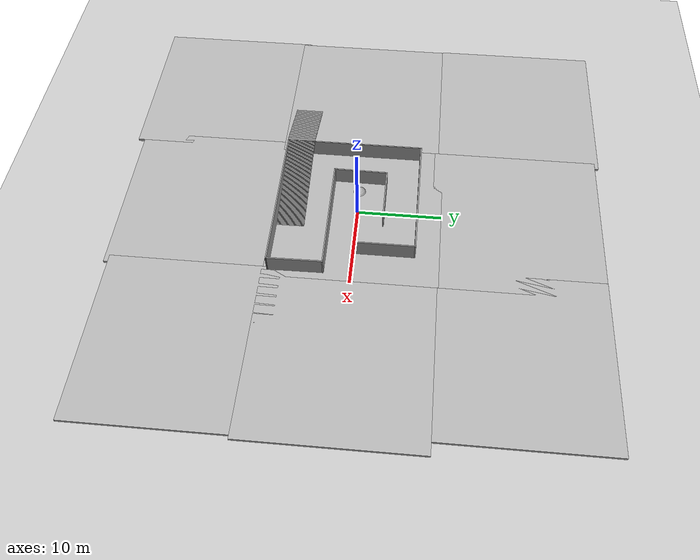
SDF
<sdf version="1.6">
 <world name="default">
  <physics name="default_physics" default="0" type="ode">
   <max_step_size>0.003</max_step_size>
   <real_time_factor>1</real_time_factor>
   <ode>
    <solver>
     <type>quick</type>
     <iters>100</iters>
     <sor>1.3</sor>
     <use_dynamic_moi_rescaling>0</use_dynamic_moi_rescaling>
    </solver>
    <constraints>
     <cfm>0</cfm>
     <erp>0.2</erp>
     <contact_max_correcting_vel>100</contact_max_correcting_vel>
     <contact_surface_layer>0.001</contact_surface_layer>
    </constraints>
   </ode>
   <real_time_update_rate>1000</real_time_update_rate>
  </physics>
  <spherical_coordinates>
   <latitude_deg>40</latitude_deg>
   <longitude_deg>40</longitude_deg>
  </spherical_coordinates>
  <light name="sun" type="directional">
   <pose>0 0 10 0 -0 0</pose>
   <diffuse>0.8 0.8 0.8 1</diffuse>
   <specular>0.1 0.1 0.1 1</specular>
   <attenuation>
    <range>1000</range>
    <constant>0.9</constant>
    <linear>0.01</linear>
    <quadratic>0.001</quadratic>
   </attenuation>
   <direction>-0.5 0.5 -1</direction>
  </light>
  <model name="ground_plane">
   <static>1</static>
   <link name="link">
    <collision name="collision">
     <geometry><plane><normal>0 0 1</normal><size>100 100</size></plane></geometry>
     <surface><friction><ode><mu>100</mu><mu2>50</mu2></ode></friction></surface>
    </collision>
    <visual name="visual">
     <cast_shadows>0</cast_shadows>
     <geometry><plane><normal>0 0 1</normal><size>100 100</size></plane></geometry>
     <material>
      <script><uri>file://media/materials/scripts/gazebo.material</uri><name>Gazebo/Grey</name></script>
     </material>
    </visual>
   </link>
  </model>
  <model name="box">
   <static>1</static>
   <link name="box">
    <visual name="visual"><geometry><box><size>20 20 0.5</size></box></geometry></visual>
    <collision name="visual">
     <geometry><box><size>20 20 0.5</size></box></geometry>
     <surface><friction><ode><mu>0.2</mu><mu2>0.2</mu2></ode></friction></surface>
    </collision>
   </link>
  </model>
  <model name="box2">
   <static>1</static>
   <pose>-1 -1 0 0 -0 0</pose>
   <link name="box2">
    <visual name="visual2"><geometry><box><size>2 2 0.5</size></box></geometry></visual>
    <collision name="visual2"><geometry><box><size>2 2 0.5</size></box></geometry></collision>
   </link>
  </model>
  <model name="sph">
   <static>1</static>
   <pose>-3 0 -0.4 0 -0 0</pose>
   <link name="box2">
    <visual name="visual2"><geometry><sphere><radius>1</radius></sphere></geometry></visual>
    <collision name="visual2"><geometry><sphere><radius>1</radius></sphere></geometry></collision>
   </link>
  </model>
  <gravity>0 0 -9.8</gravity>
  <magnetic_field>6e-06 2.3e-05 -4.2e-05</magnetic_field>
  <atmosphere type="adiabatic"/>
  <scene><ambient>0.4 0.4 0.4 1</ambient><background>0.7 0.7 0.7 1</background><shadows>1</shadows></scene>
  <spherical_coordinates>
   <surface_model>EARTH_WGS84</surface_model>
   <latitude_deg>0</latitude_deg>
   <longitude_deg>0</longitude_deg>
   <elevation>0</elevation>
   <heading_deg>0</heading_deg>
  </spherical_coordinates>
  <model name="box_clone">
   <static>1</static>
   <pose>-19.0505 -0.235094 0 0 -0 0</pose>
   <link name="box">
    <visual name="visual"><geometry><box><size>20 20 0.5</size></box></geometry></visual>
    <collision name="visual">
     <geometry><box><size>20 20 0.5</size></box></geometry>
     <surface><friction><ode><mu>0.2</mu><mu2>0.2</mu2></ode></friction></surface>
    </collision>
   </link>
  </model>
  <model name="box_clone_0">
   <static>1</static>
   <pose>-19.1652 19.4103 0 0 -0 0</pose>
   <link name="box">
    <visual name="visual"><geometry><box><size>20 20 0.5</size></box></geometry></visual>
    <collision name="visual">
     <geometry><box><size>20 20 0.5</size></box></geometry>
     <surface><friction><ode><mu>0.2</mu><mu2>0.2</mu2></ode></friction></surface>
    </collision>
   </link>
  </model>
  <model name="box_clone_1">
   <static>1</static>
   <pose>-0.009698 18.9587 0 0 -0 0</pose>
   <link name="box">
    <visual name="visual"><geometry><box><size>20 20 0.5</size></box></geometry></visual>
    <collision name="visual">
     <geometry><box><size>20 20 0.5</size></box></geometry>
     <surface><friction><ode><mu>0.2</mu><mu2>0.2</mu2></ode></friction></surface>
    </collision>
   </link>
  </model>
  <model name="box_clone_2">
   <static>1</static>
   <pose>17.7917 18.98 0 0 -0 0</pose>
   <link name="box">
    <visual name="visual"><geometry><box><size>20 20 0.5</size></box></geometry></visual>
    <collision name="visual">
     <geometry><box><size>20 20 0.5</size></box></geometry>
     <surface><friction><ode><mu>0.2</mu><mu2>0.2</mu2></ode></friction></surface>
    </collision>
   </link>
  </model>
  <model name="box_clone_3">
   <static>1</static>
   <pose>19.2214 -0.144455 0 0 -0 0</pose>
   <link name="box">
    <visual name="visual"><geometry><box><size>20 20 0.5</size></box></geometry></visual>
    <collision name="visual">
     <geometry><box><size>20 20 0.5</size></box></geometry>
     <surface><friction><ode><mu>0.2</mu><mu2>0.2</mu2></ode></friction></surface>
    </collision>
   </link>
  </model>
  <model name="box_clone_4">
   <static>1</static>
   <pose>-0.304111 -18.3731 0 0 -0 0</pose>
   <link name="box">
    <visual name="visual"><geometry><box><size>20 20 0.5</size></box></geometry></visual>
    <collision name="visual">
     <geometry><box><size>20 20 0.5</size></box></geometry>
     <surface><friction><ode><mu>0.2</mu><mu2>0.2</mu2></ode></friction></surface>
    </collision>
   </link>
  </model>
  <model name="box_clone_5">
   <static>1</static>
   <pose>-19.1918 -19.1964 0 0 -0 0</pose>
   <link name="box">
    <visual name="visual"><geometry><box><size>20 20 0.5</size></box></geometry></visual>
    <collision name="visual">
     <geometry><box><size>20 20 0.5</size></box></geometry>
     <surface><friction><ode><mu>0.2</mu><mu2>0.2</mu2></ode></friction></surface>
    </collision>
   </link>
  </model>
  <model name="box_clone_6">
   <static>1</static>
   <pose>18.8151 -17.8765 0 0 -0 0</pose>
   <link name="box">
    <visual name="visual"><geometry><box><size>20 20 0.5</size></box></geometry></visual>
    <collision name="visual">
     <geometry><box><size>20 20 0.5</size></box></geometry>
     <surface><friction><ode><mu>0.2</mu><mu2>0.2</mu2></ode></friction></surface>
    </collision>
   </link>
  </model>
  <model name="Ramp">
   <pose>-3.77089 -1.15955 0 0 -0 0</pose>
   <link name="Stairs_1">
    <visual name="Stairs_1_Visual_0">
     <pose>7.69041 -6.6539 0.0125 0 -0 -1.5708</pose>
     <geometry><box><size>3.41406 0.127471 0.025</size></box></geometry>
     <material>
      <script><uri>file://media/materials/scripts/gazebo.material</uri><name>Gazebo/Grey</name></script>
      <ambient>1 1 1 1</ambient>
     </material>
    </visual>
    <collision name="Stairs_1_Collision_0">
     <geometry><box><size>3.41406 0.127471 0.025</size></box></geometry>
     <pose>7.69041 -6.6539 0.0125 0 -0 -1.5708</pose>
    </collision>
    <visual name="Stairs_1_Visual_1">
     <pose>7.56294 -6.6539 0.0375 0 -0 -1.5708</pose>
     <geometry><box><size>3.41406 0.127471 0.025</size></box></geometry>
     <material>
      <script><uri>file://media/materials/scripts/gazebo.material</uri><name>Gazebo/Grey</name></script>
      <ambient>1 1 1 1</ambient>
     </material>
    </visual>
    <collision name="Stairs_1_Collision_1">
     <geometry><box><size>3.41406 0.127471 0.025</size></box></geometry>
     <pose>7.56294 -6.6539 0.0375 0 -0 -1.5708</pose>
    </collision>
    <visual name="Stairs_1_Visual_2">
     <pose>7.43547 -6.6539 0.0625 0 -0 -1.5708</pose>
     <geometry><box><size>3.41406 0.127471 0.025</size></box></geometry>
     <material>
      <script><uri>file://media/materials/scripts/gazebo.material</uri><name>Gazebo/Grey</name></script>
      <ambient>1 1 1 1</ambient>
     </material>
    </visual>
    <collision name="Stairs_1_Collision_2">
     <geometry><box><size>3.41406 0.127471 0.025</size></box></geometry>
     <pose>7.43547 -6.6539 0.0625 0 -0 -1.5708</pose>
    </collision>
    <visual name="Stairs_1_Visual_3">
     <pose>7.308 -6.6539 0.0875 0 -0 -1.5708</pose>
     <geometry><box><size>3.41406 0.127471 0.025</size></box></geometry>
     <material>
      <script><uri>file://media/materials/scripts/gazebo.material</uri><name>Gazebo/Grey</name></script>
      <ambient>1 1 1 1</ambient>
     </material>
    </visual>
    <collision name="Stairs_1_Collision_3">
     <geometry><box><size>3.41406 0.127471 0.025</size></box></geometry>
     <pose>7.308 -6.6539 0.0875 0 -0 -1.5708</pose>
    </collision>
    <visual name="Stairs_1_Visual_4">
     <pose>7.18053 -6.6539 0.1125 0 -0 -1.5708</pose>
     <geometry><box><size>3.41406 0.127471 0.025</size></box></geometry>
     <material>
      <script><uri>file://media/materials/scripts/gazebo.material</uri><name>Gazebo/Grey</name></script>
      <ambient>1 1 1 1</ambient>
     </material>
    </visual>
    <collision name="Stairs_1_Collision_4">
     <geometry><box><size>3.41406 0.127471 0.025</size></box></geometry>
     <pose>7.18053 -6.6539 0.1125 0 -0 -1.5708</pose>
    </collision>
    <visual name="Stairs_1_Visual_5">
     <pose>7.05306 -6.6539 0.1375 0 -0 -1.5708</pose>
     <geometry><box><size>3.41406 0.127471 0.025</size></box></geometry>
     <material>
      <script><uri>file://media/materials/scripts/gazebo.material</uri><name>Gazebo/Grey</name></script>
      <ambient>1 1 1 1</ambient>
     </material>
    </visual>
    <collision name="Stairs_1_Collision_5">
     <geometry><box><size>3.41406 0.127471 0.025</size></box></geometry>
     <pose>7.05306 -6.6539 0.1375 0 -0 -1.5708</pose>
    </collision>
    <visual name="Stairs_1_Visual_6">
     <pose>6.92559 -6.6539 0.1625 0 -0 -1.5708</pose>
     <geometry><box><size>3.41406 0.127471 0.025</size></box></geometry>
     <material>
      <script><uri>file://media/materials/scripts/gazebo.material</uri><name>Gazebo/Grey</name></script>
      <ambient>1 1 1 1</ambient>
     </material>
    </visual>
    <collision name="Stairs_1_Collision_6">
     <geometry><box><size>3.41406 0.127471 0.025</size></box></geometry>
     <pose>6.92559 -6.6539 0.1625 0 -0 -1.5708</pose>
    </collision>
    <visual name="Stairs_1_Visual_7">
     <pose>6.79812 -6.6539 0.1875 0 -0 -1.5708</pose>
     <geometry><box><size>3.41406 0.127471 0.025</size></box></geometry>
     <material>
      <script><uri>file://media/materials/scripts/gazebo.material</uri><name>Gazebo/Grey</name></script>
      <ambient>1 1 1 1</ambient>
     </material>
    </visual>
    <collision name="Stairs_1_Collision_7">
     <geometry><box><size>3.41406 0.127471 0.025</size></box></geometry>
     <pose>6.79812 -6.6539 0.1875 0 -0 -1.5708</pose>
    </collision>
    <visual name="Stairs_1_Visual_8">
     <pose>6.67065 -6.6539 0.2125 0 -0 -1.5708</pose>
     <geometry><box><size>3.41406 0.127471 0.025</size></box></geometry>
     <material>
      <script><uri>file://media/materials/scripts/gazebo.material</uri><name>Gazebo/Grey</name></script>
      <ambient>1 1 1 1</ambient>
     </material>
    </visual>
    <collision name="Stairs_1_Collision_8">
     <geometry><box><size>3.41406 0.127471 0.025</size></box></geometry>
     <pose>6.67065 -6.6539 0.2125 0 -0 -1.5708</pose>
    </collision>
    <visual name="Stairs_1_Visual_9">
     <pose>6.54317 -6.6539 0.2375 0 -0 -1.5708</pose>
     <geometry><box><size>3.41406 0.127471 0.025</size></box></geometry>
     <material>
      <script><uri>file://media/materials/scripts/gazebo.material</uri><name>Gazebo/Grey</name></script>
      <ambient>1 1 1 1</ambient>
     </material>
    </visual>
    <collision name="Stairs_1_Collision_9">
     <geometry><box><size>3.41406 0.127471 0.025</size></box></geometry>
     <pose>6.54317 -6.6539 0.2375 0 -0 -1.5708</pose>
    </collision>
    <visual name="Stairs_1_Visual_10">
     <pose>6.4157 -6.6539 0.2625 0 -0 -1.5708</pose>
     <geometry><box><size>3.41406 0.127471 0.025</size></box></geometry>
     <material>
      <script><uri>file://media/materials/scripts/gazebo.material</uri><name>Gazebo/Grey</name></script>
      <ambient>1 1 1 1</ambient>
     </material>
    </visual>
    <collision name="Stairs_1_Collision_10">
     <geometry><box><size>3.41406 0.127471 0.025</size></box></geometry>
     <pose>6.4157 -6.6539 0.2625 0 -0 -1.5708</pose>
    </collision>
    <visual name="Stairs_1_Visual_11">
     <pose>6.28823 -6.6539 0.2875 0 -0 -1.5708</pose>
     <geometry><box><size>3.41406 0.127471 0.025</size></box></geometry>
     <material>
      <script><uri>file://media/materials/scripts/gazebo.material</uri><name>Gazebo/Grey</name></script>
      <ambient>1 1 1 1</ambient>
     </material>
    </visual>
    <collision name="Stairs_1_Collision_11">
     <geometry><box><size>3.41406 0.127471 0.025</size></box></geometry>
     <pose>6.28823 -6.6539 0.2875 0 -0 -1.5708</pose>
    </collision>
    <visual name="Stairs_1_Visual_12">
     <pose>6.16076 -6.6539 0.3125 0 -0 -1.5708</pose>
     <geometry><box><size>3.41406 0.127471 0.025</size></box></geometry>
     <material>
      <script><uri>file://media/materials/scripts/gazebo.material</uri><name>Gazebo/Grey</name></script>
      <ambient>1 1 1 1</ambient>
     </material>
    </visual>
    <collision name="Stairs_1_Collision_12">
     <geometry><box><size>3.41406 0.127471 0.025</size></box></geometry>
     <pose>6.16076 -6.6539 0.3125 0 -0 -1.5708</pose>
    </collision>
    <visual name="Stairs_1_Visual_13">
     <pose>6.03329 -6.6539 0.3375 0 -0 -1.5708</pose>
     <geometry><box><size>3.41406 0.127471 0.025</size></box></geometry>
     <material>
      <script><uri>file://media/materials/scripts/gazebo.material</uri><name>Gazebo/Grey</name></script>
      <ambient>1 1 1 1</ambient>
     </material>
    </visual>
    <collision name="Stairs_1_Collision_13">
     <geometry><box><size>3.41406 0.127471 0.025</size></box></geometry>
     <pose>6.03329 -6.6539 0.3375 0 -0 -1.5708</pose>
    </collision>
    <visual name="Stairs_1_Visual_14">
     <pose>5.90582 -6.6539 0.3625 0 -0 -1.5708</pose>
     <geometry><box><size>3.41406 0.127471 0.025</size></box></geometry>
     <material>
      <script><uri>file://media/materials/scripts/gazebo.material</uri><name>Gazebo/Grey</name></script>
      <ambient>1 1 1 1</ambient>
     </material>
    </visual>
    <collision name="Stairs_1_Collision_14">
     <geometry><box><size>3.41406 0.127471 0.025</size></box></geometry>
     <pose>5.90582 -6.6539 0.3625 0 -0 -1.5708</pose>
    </collision>
    <visual name="Stairs_1_Visual_15">
     <pose>5.77835 -6.6539 0.3875 0 -0 -1.5708</pose>
     <geometry><box><size>3.41406 0.127471 0.025</size></box></geometry>
     <material>
      <script><uri>file://media/materials/scripts/gazebo.material</uri><name>Gazebo/Grey</name></script>
      <ambient>1 1 1 1</ambient>
     </material>
    </visual>
    <collision name="Stairs_1_Collision_15">
     <geometry><box><size>3.41406 0.127471 0.025</size></box></geometry>
     <pose>5.77835 -6.6539 0.3875 0 -0 -1.5708</pose>
    </collision>
    <visual name="Stairs_1_Visual_16">
     <pose>5.65088 -6.6539 0.4125 0 -0 -1.5708</pose>
     <geometry><box><size>3.41406 0.127471 0.025</size></box></geometry>
     <material>
      <script><uri>file://media/materials/scripts/gazebo.material</uri><name>Gazebo/Grey</name></script>
      <ambient>1 1 1 1</ambient>
     </material>
    </visual>
    <collision name="Stairs_1_Collision_16">
     <geometry><box><size>3.41406 0.127471 0.025</size></box></geometry>
     <pose>5.65088 -6.6539 0.4125 0 -0 -1.5708</pose>
    </collision>
    <visual name="Stairs_1_Visual_17">
     <pose>5.52341 -6.6539 0.4375 0 -0 -1.5708</pose>
     <geometry><box><size>3.41406 0.127471 0.025</size></box></geometry>
     <material>
      <script><uri>file://media/materials/scripts/gazebo.material</uri><name>Gazebo/Grey</name></script>
      <ambient>1 1 1 1</ambient>
     </material>
    </visual>
    <collision name="Stairs_1_Collision_17">
     <geometry><box><size>3.41406 0.127471 0.025</size></box></geometry>
     <pose>5.52341 -6.6539 0.4375 0 -0 -1.5708</pose>
    </collision>
    <visual name="Stairs_1_Visual_18">
     <pose>5.39594 -6.6539 0.4625 0 -0 -1.5708</pose>
     <geometry><box><size>3.41406 0.127471 0.025</size></box></geometry>
     <material>
      <script><uri>file://media/materials/scripts/gazebo.material</uri><name>Gazebo/Grey</name></script>
      <ambient>1 1 1 1</ambient>
     </material>
    </visual>
    <collision name="Stairs_1_Collision_18">
     <geometry><box><size>3.41406 0.127471 0.025</size></box></geometry>
     <pose>5.39594 -6.6539 0.4625 0 -0 -1.5708</pose>
    </collision>
    <visual name="Stairs_1_Visual_19">
     <pose>5.26847 -6.6539 0.4875 0 -0 -1.5708</pose>
     <geometry><box><size>3.41406 0.127471 0.025</size></box></geometry>
     <material>
      <script><uri>file://media/materials/scripts/gazebo.material</uri><name>Gazebo/Grey</name></script>
      <ambient>1 1 1 1</ambient>
     </material>
    </visual>
    <collision name="Stairs_1_Collision_19">
     <geometry><box><size>3.41406 0.127471 0.025</size></box></geometry>
     <pose>5.26847 -6.6539 0.4875 0 -0 -1.5708</pose>
    </collision>
    <visual name="Stairs_1_Visual_20">
     <pose>5.14099 -6.6539 0.5125 0 -0 -1.5708</pose>
     <geometry><box><size>3.41406 0.127471 0.025</size></box></geometry>
     <material>
      <script><uri>file://media/materials/scripts/gazebo.material</uri><name>Gazebo/Grey</name></script>
      <ambient>1 1 1 1</ambient>
     </material>
    </visual>
    <collision name="Stairs_1_Collision_20">
     <geometry><box><size>3.41406 0.127471 0.025</size></box></geometry>
     <pose>5.14099 -6.6539 0.5125 0 -0 -1.5708</pose>
    </collision>
    <visual name="Stairs_1_Visual_21">
     <pose>5.01352 -6.6539 0.5375 0 -0 -1.5708</pose>
     <geometry><box><size>3.41406 0.127471 0.025</size></box></geometry>
     <material>
      <script><uri>file://media/materials/scripts/gazebo.material</uri><name>Gazebo/Grey</name></script>
      <ambient>1 1 1 1</ambient>
     </material>
    </visual>
    <collision name="Stairs_1_Collision_21">
     <geometry><box><size>3.41406 0.127471 0.025</size></box></geometry>
     <pose>5.01352 -6.6539 0.5375 0 -0 -1.5708</pose>
    </collision>
    <visual name="Stairs_1_Visual_22">
     <pose>4.88605 -6.6539 0.5625 0 -0 -1.5708</pose>
     <geometry><box><size>3.41406 0.127471 0.025</size></box></geometry>
     <material>
      <script><uri>file://media/materials/scripts/gazebo.material</uri><name>Gazebo/Grey</name></script>
      <ambient>1 1 1 1</ambient>
     </material>
    </visual>
    <collision name="Stairs_1_Collision_22">
     <geometry><box><size>3.41406 0.127471 0.025</size></box></geometry>
     <pose>4.88605 -6.6539 0.5625 0 -0 -1.5708</pose>
    </collision>
    <visual name="Stairs_1_Visual_23">
     <pose>4.75858 -6.6539 0.5875 0 -0 -1.5708</pose>
     <geometry><box><size>3.41406 0.127471 0.025</size></box></geometry>
     <material>
      <script><uri>file://media/materials/scripts/gazebo.material</uri><name>Gazebo/Grey</name></script>
      <ambient>1 1 1 1</ambient>
     </material>
    </visual>
    <collision name="Stairs_1_Collision_23">
     <geometry><box><size>3.41406 0.127471 0.025</size></box></geometry>
     <pose>4.75858 -6.6539 0.5875 0 -0 -1.5708</pose>
    </collision>
    <visual name="Stairs_1_Visual_24">
     <pose>4.63111 -6.6539 0.6125 0 -0 -1.5708</pose>
     <geometry><box><size>3.41406 0.127471 0.025</size></box></geometry>
     <material>
      <script><uri>file://media/materials/scripts/gazebo.material</uri><name>Gazebo/Grey</name></script>
      <ambient>1 1 1 1</ambient>
     </material>
    </visual>
    <collision name="Stairs_1_Collision_24">
     <geometry><box><size>3.41406 0.127471 0.025</size></box></geometry>
     <pose>4.63111 -6.6539 0.6125 0 -0 -1.5708</pose>
    </collision>
    <visual name="Stairs_1_Visual_25">
     <pose>4.50364 -6.6539 0.6375 0 -0 -1.5708</pose>
     <geometry><box><size>3.41406 0.127471 0.025</size></box></geometry>
     <material>
      <script><uri>file://media/materials/scripts/gazebo.material</uri><name>Gazebo/Grey</name></script>
      <ambient>1 1 1 1</ambient>
     </material>
    </visual>
    <collision name="Stairs_1_Collision_25">
     <geometry><box><size>3.41406 0.127471 0.025</size></box></geometry>
     <pose>4.50364 -6.6539 0.6375 0 -0 -1.5708</pose>
    </collision>
    <visual name="Stairs_1_Visual_26">
     <pose>4.37617 -6.6539 0.6625 0 -0 -1.5708</pose>
     <geometry><box><size>3.41406 0.127471 0.025</size></box></geometry>
     <material>
      <script><uri>file://media/materials/scripts/gazebo.material</uri><name>Gazebo/Grey</name></script>
      <ambient>1 1 1 1</ambient>
     </material>
    </visual>
    <collision name="Stairs_1_Collision_26">
     <geometry><box><size>3.41406 0.127471 0.025</size></box></geometry>
     <pose>4.37617 -6.6539 0.6625 0 -0 -1.5708</pose>
    </collision>
    <visual name="Stairs_1_Visual_27">
     <pose>4.2487 -6.6539 0.6875 0 -0 -1.5708</pose>
     <geometry><box><size>3.41406 0.127471 0.025</size></box></geometry>
     <material>
      <script><uri>file://media/materials/scripts/gazebo.material</uri><name>Gazebo/Grey</name></script>
      <ambient>1 1 1 1</ambient>
     </material>
    </visual>
    <collision name="Stairs_1_Collision_27">
     <geometry><box><size>3.41406 0.127471 0.025</size></box></geometry>
     <pose>4.2487 -6.6539 0.6875 0 -0 -1.5708</pose>
    </collision>
    <visual name="Stairs_1_Visual_28">
     <pose>4.12123 -6.6539 0.7125 0 -0 -1.5708</pose>
     <geometry><box><size>3.41406 0.127471 0.025</size></box></geometry>
     <material>
      <script><uri>file://media/materials/scripts/gazebo.material</uri><name>Gazebo/Grey</name></script>
      <ambient>1 1 1 1</ambient>
     </material>
    </visual>
    <collision name="Stairs_1_Collision_28">
     <geometry><box><size>3.41406 0.127471 0.025</size></box></geometry>
     <pose>4.12123 -6.6539 0.7125 0 -0 -1.5708</pose>
    </collision>
    <visual name="Stairs_1_Visual_29">
     <pose>3.99376 -6.6539 0.7375 0 -0 -1.5708</pose>
     <geometry><box><size>3.41406 0.127471 0.025</size></box></geometry>
     <material>
      <script><uri>file://media/materials/scripts/gazebo.material</uri><name>Gazebo/Grey</name></script>
      <ambient>1 1 1 1</ambient>
     </material>
    </visual>
    <collision name="Stairs_1_Collision_29">
     <geometry><box><size>3.41406 0.127471 0.025</size></box></geometry>
     <pose>3.99376 -6.6539 0.7375 0 -0 -1.5708</pose>
    </collision>
    <visual name="Stairs_1_Visual_30">
     <pose>3.86628 -6.6539 0.7625 0 -0 -1.5708</pose>
     <geometry><box><size>3.41406 0.127471 0.025</size></box></geometry>
     <material>
      <script><uri>file://media/materials/scripts/gazebo.material</uri><name>Gazebo/Grey</name></script>
      <ambient>1 1 1 1</ambient>
     </material>
    </visual>
    <collision name="Stairs_1_Collision_30">
     <geometry><box><size>3.41406 0.127471 0.025</size></box></geometry>
     <pose>3.86628 -6.6539 0.7625 0 -0 -1.5708</pose>
    </collision>
    <visual name="Stairs_1_Visual_31">
     <pose>3.73881 -6.6539 0.7875 0 -0 -1.5708</pose>
     <geometry><box><size>3.41406 0.127471 0.025</size></box></geometry>
     <material>
      <script><uri>file://media/materials/scripts/gazebo.material</uri><name>Gazebo/Grey</name></script>
      <ambient>1 1 1 1</ambient>
     </material>
    </visual>
    <collision name="Stairs_1_Collision_31">
     <geometry><box><size>3.41406 0.127471 0.025</size></box></geometry>
     <pose>3.73881 -6.6539 0.7875 0 -0 -1.5708</pose>
    </collision>
    <visual name="Stairs_1_Visual_32">
     <pose>3.61134 -6.6539 0.8125 0 -0 -1.5708</pose>
     <geometry><box><size>3.41406 0.127471 0.025</size></box></geometry>
     <material>
      <script><uri>file://media/materials/scripts/gazebo.material</uri><name>Gazebo/Grey</name></script>
      <ambient>1 1 1 1</ambient>
     </material>
    </visual>
    <collision name="Stairs_1_Collision_32">
     <geometry><box><size>3.41406 0.127471 0.025</size></box></geometry>
     <pose>3.61134 -6.6539 0.8125 0 -0 -1.5708</pose>
    </collision>
    <visual name="Stairs_1_Visual_33">
     <pose>3.48387 -6.6539 0.8375 0 -0 -1.5708</pose>
     <geometry><box><size>3.41406 0.127471 0.025</size></box></geometry>
     <material>
      <script><uri>file://media/materials/scripts/gazebo.material</uri><name>Gazebo/Grey</name></script>
      <ambient>1 1 1 1</ambient>
     </material>
    </visual>
    <collision name="Stairs_1_Collision_33">
     <geometry><box><size>3.41406 0.127471 0.025</size></box></geometry>
     <pose>3.48387 -6.6539 0.8375 0 -0 -1.5708</pose>
    </collision>
    <visual name="Stairs_1_Visual_34">
     <pose>3.3564 -6.6539 0.8625 0 -0 -1.5708</pose>
     <geometry><box><size>3.41406 0.127471 0.025</size></box></geometry>
     <material>
      <script><uri>file://media/materials/scripts/gazebo.material</uri><name>Gazebo/Grey</name></script>
      <ambient>1 1 1 1</ambient>
     </material>
    </visual>
    <collision name="Stairs_1_Collision_34">
     <geometry><box><size>3.41406 0.127471 0.025</size></box></geometry>
     <pose>3.3564 -6.6539 0.8625 0 -0 -1.5708</pose>
    </collision>
    <visual name="Stairs_1_Visual_35">
     <pose>3.22893 -6.6539 0.8875 0 -0 -1.5708</pose>
     <geometry><box><size>3.41406 0.127471 0.025</size></box></geometry>
     <material>
      <script><uri>file://media/materials/scripts/gazebo.material</uri><name>Gazebo/Grey</name></script>
      <ambient>1 1 1 1</ambient>
     </material>
    </visual>
    <collision name="Stairs_1_Collision_35">
     <geometry><box><size>3.41406 0.127471 0.025</size></box></geometry>
     <pose>3.22893 -6.6539 0.8875 0 -0 -1.5708</pose>
    </collision>
    <visual name="Stairs_1_Visual_36">
     <pose>3.10146 -6.6539 0.9125 0 -0 -1.5708</pose>
     <geometry><box><size>3.41406 0.127471 0.025</size></box></geometry>
     <material>
      <script><uri>file://media/materials/scripts/gazebo.material</uri><name>Gazebo/Grey</name></script>
      <ambient>1 1 1 1</ambient>
     </material>
    </visual>
    <collision name="Stairs_1_Collision_36">
     <geometry><box><size>3.41406 0.127471 0.025</size></box></geometry>
     <pose>3.10146 -6.6539 0.9125 0 -0 -1.5708</pose>
    </collision>
    <visual name="Stairs_1_Visual_37">
     <pose>2.97399 -6.6539 0.9375 0 -0 -1.5708</pose>
     <geometry><box><size>3.41406 0.127471 0.025</size></box></geometry>
     <material>
      <script><uri>file://media/materials/scripts/gazebo.material</uri><name>Gazebo/Grey</name></script>
      <ambient>1 1 1 1</ambient>
     </material>
    </visual>
    <collision name="Stairs_1_Collision_37">
     <geometry><box><size>3.41406 0.127471 0.025</size></box></geometry>
     <pose>2.97399 -6.6539 0.9375 0 -0 -1.5708</pose>
    </collision>
    <visual name="Stairs_1_Visual_38">
     <pose>2.84652 -6.6539 0.9625 0 -0 -1.5708</pose>
     <geometry><box><size>3.41406 0.127471 0.025</size></box></geometry>
     <material>
      <script><uri>file://media/materials/scripts/gazebo.material</uri><name>Gazebo/Grey</name></script>
      <ambient>1 1 1 1</ambient>
     </material>
    </visual>
    <collision name="Stairs_1_Collision_38">
     <geometry><box><size>3.41406 0.127471 0.025</size></box></geometry>
     <pose>2.84652 -6.6539 0.9625 0 -0 -1.5708</pose>
    </collision>
    <visual name="Stairs_1_Visual_39">
     <pose>2.71905 -6.6539 0.9875 0 -0 -1.5708</pose>
     <geometry><box><size>3.41406 0.127471 0.025</size></box></geometry>
     <material>
      <script><uri>file://media/materials/scripts/gazebo.material</uri><name>Gazebo/Grey</name></script>
      <ambient>1 1 1 1</ambient>
     </material>
    </visual>
    <collision name="Stairs_1_Collision_39">
     <geometry><box><size>3.41406 0.127471 0.025</size></box></geometry>
     <pose>2.71905 -6.6539 0.9875 0 -0 -1.5708</pose>
    </collision>
    <visual name="Stairs_1_Visual_40">
     <pose>2.59158 -6.6539 1.0125 0 -0 -1.5708</pose>
     <geometry><box><size>3.41406 0.127471 0.025</size></box></geometry>
     <material>
      <script><uri>file://media/materials/scripts/gazebo.material</uri><name>Gazebo/Grey</name></script>
      <ambient>1 1 1 1</ambient>
     </material>
    </visual>
    <collision name="Stairs_1_Collision_40">
     <geometry><box><size>3.41406 0.127471 0.025</size></box></geometry>
     <pose>2.59158 -6.6539 1.0125 0 -0 -1.5708</pose>
    </collision>
    <visual name="Stairs_1_Visual_41">
     <pose>2.4641 -6.6539 1.0375 0 -0 -1.5708</pose>
     <geometry><box><size>3.41406 0.127471 0.025</size></box></geometry>
     <material>
      <script><uri>file://media/materials/scripts/gazebo.material</uri><name>Gazebo/Grey</name></script>
      <ambient>1 1 1 1</ambient>
     </material>
    </visual>
    <collision name="Stairs_1_Collision_41">
     <geometry><box><size>3.41406 0.127471 0.025</size></box></geometry>
     <pose>2.4641 -6.6539 1.0375 0 -0 -1.5708</pose>
    </collision>
    <visual name="Stairs_1_Visual_42">
     <pose>2.33663 -6.6539 1.0625 0 -0 -1.5708</pose>
     <geometry><box><size>3.41406 0.127471 0.025</size></box></geometry>
     <material>
      <script><uri>file://media/materials/scripts/gazebo.material</uri><name>Gazebo/Grey</name></script>
      <ambient>1 1 1 1</ambient>
     </material>
    </visual>
    <collision name="Stairs_1_Collision_42">
     <geometry><box><size>3.41406 0.127471 0.025</size></box></geometry>
     <pose>2.33663 -6.6539 1.0625 0 -0 -1.5708</pose>
    </collision>
    <visual name="Stairs_1_Visual_43">
     <pose>2.20916 -6.6539 1.0875 0 -0 -1.5708</pose>
     <geometry><box><size>3.41406 0.127471 0.025</size></box></geometry>
     <material>
      <script><uri>file://media/materials/scripts/gazebo.material</uri><name>Gazebo/Grey</name></script>
      <ambient>1 1 1 1</ambient>
     </material>
    </visual>
    <collision name="Stairs_1_Collision_43">
     <geometry><box><size>3.41406 0.127471 0.025</size></box></geometry>
     <pose>2.20916 -6.6539 1.0875 0 -0 -1.5708</pose>
    </collision>
    <visual name="Stairs_1_Visual_44">
     <pose>2.08169 -6.6539 1.1125 0 -0 -1.5708</pose>
     <geometry><box><size>3.41406 0.127471 0.025</size></box></geometry>
     <material>
      <script><uri>file://media/materials/scripts/gazebo.material</uri><name>Gazebo/Grey</name></script>
      <ambient>1 1 1 1</ambient>
     </material>
    </visual>
    <collision name="Stairs_1_Collision_44">
     <geometry><box><size>3.41406 0.127471 0.025</size></box></geometry>
     <pose>2.08169 -6.6539 1.1125 0 -0 -1.5708</pose>
    </collision>
    <visual name="Stairs_1_Visual_45">
     <pose>1.95422 -6.6539 1.1375 0 -0 -1.5708</pose>
     <geometry><box><size>3.41406 0.127471 0.025</size></box></geometry>
     <material>
      <script><uri>file://media/materials/scripts/gazebo.material</uri><name>Gazebo/Grey</name></script>
      <ambient>1 1 1 1</ambient>
     </material>
    </visual>
    <collision name="Stairs_1_Collision_45">
     <geometry><box><size>3.41406 0.127471 0.025</size></box></geometry>
     <pose>1.95422 -6.6539 1.1375 0 -0 -1.5708</pose>
    </collision>
    <visual name="Stairs_1_Visual_46">
     <pose>1.82675 -6.6539 1.1625 0 -0 -1.5708</pose>
     <geometry><box><size>3.41406 0.127471 0.025</size></box></geometry>
     <material>
      <script><uri>file://media/materials/scripts/gazebo.material</uri><name>Gazebo/Grey</name></script>
      <ambient>1 1 1 1</ambient>
     </material>
    </visual>
    <collision name="Stairs_1_Collision_46">
     <geometry><box><size>3.41406 0.127471 0.025</size></box></geometry>
     <pose>1.82675 -6.6539 1.1625 0 -0 -1.5708</pose>
    </collision>
    <visual name="Stairs_1_Visual_47">
     <pose>1.69928 -6.6539 1.1875 0 -0 -1.5708</pose>
     <geometry><box><size>3.41406 0.127471 0.025</size></box></geometry>
     <material>
      <script><uri>file://media/materials/scripts/gazebo.material</uri><name>Gazebo/Grey</name></script>
      <ambient>1 1 1 1</ambient>
     </material>
    </visual>
    <collision name="Stairs_1_Collision_47">
     <geometry><box><size>3.41406 0.127471 0.025</size></box></geometry>
     <pose>1.69928 -6.6539 1.1875 0 -0 -1.5708</pose>
    </collision>
    <visual name="Stairs_1_Visual_48">
     <pose>1.57181 -6.6539 1.2125 0 -0 -1.5708</pose>
     <geometry><box><size>3.41406 0.127471 0.025</size></box></geometry>
     <material>
      <script><uri>file://media/materials/scripts/gazebo.material</uri><name>Gazebo/Grey</name></script>
      <ambient>1 1 1 1</ambient>
     </material>
    </visual>
    <collision name="Stairs_1_Collision_48">
     <geometry><box><size>3.41406 0.127471 0.025</size></box></geometry>
     <pose>1.57181 -6.6539 1.2125 0 -0 -1.5708</pose>
    </collision>
    <visual name="Stairs_1_Visual_49">
     <pose>1.44434 -6.6539 1.2375 0 -0 -1.5708</pose>
     <geometry><box><size>3.41406 0.127471 0.025</size></box></geometry>
     <material>
      <script><uri>file://media/materials/scripts/gazebo.material</uri><name>Gazebo/Grey</name></script>
      <ambient>1 1 1 1</ambient>
     </material>
    </visual>
    <collision name="Stairs_1_Collision_49">
     <geometry><box><size>3.41406 0.127471 0.025</size></box></geometry>
     <pose>1.44434 -6.6539 1.2375 0 -0 -1.5708</pose>
    </collision>
    <visual name="Stairs_1_Visual_50">
     <pose>1.31687 -6.6539 1.2625 0 -0 -1.5708</pose>
     <geometry><box><size>3.41406 0.127471 0.025</size></box></geometry>
     <material>
      <script><uri>file://media/materials/scripts/gazebo.material</uri><name>Gazebo/Grey</name></script>
      <ambient>1 1 1 1</ambient>
     </material>
    </visual>
    <collision name="Stairs_1_Collision_50">
     <geometry><box><size>3.41406 0.127471 0.025</size></box></geometry>
     <pose>1.31687 -6.6539 1.2625 0 -0 -1.5708</pose>
    </collision>
    <visual name="Stairs_1_Visual_51">
     <pose>1.18939 -6.6539 1.2875 0 -0 -1.5708</pose>
     <geometry><box><size>3.41406 0.127471 0.025</size></box></geometry>
     <material>
      <script><uri>file://media/materials/scripts/gazebo.material</uri><name>Gazebo/Grey</name></script>
      <ambient>1 1 1 1</ambient>
     </material>
    </visual>
    <collision name="Stairs_1_Collision_51">
     <geometry><box><size>3.41406 0.127471 0.025</size></box></geometry>
     <pose>1.18939 -6.6539 1.2875 0 -0 -1.5708</pose>
    </collision>
    <visual name="Stairs_1_Visual_52">
     <pose>1.06192 -6.6539 1.3125 0 -0 -1.5708</pose>
     <geometry><box><size>3.41406 0.127471 0.025</size></box></geometry>
     <material>
      <script><uri>file://media/materials/scripts/gazebo.material</uri><name>Gazebo/Grey</name></script>
      <ambient>1 1 1 1</ambient>
     </material>
    </visual>
    <collision name="Stairs_1_Collision_52">
     <geometry><box><size>3.41406 0.127471 0.025</size></box></geometry>
     <pose>1.06192 -6.6539 1.3125 0 -0 -1.5708</pose>
    </collision>
    <visual name="Stairs_1_Visual_53">
     <pose>0.934453 -6.6539 1.3375 0 -0 -1.5708</pose>
     <geometry><box><size>3.41406 0.127471 0.025</size></box></geometry>
     <material>
      <script><uri>file://media/materials/scripts/gazebo.material</uri><name>Gazebo/Grey</name></script>
      <ambient>1 1 1 1</ambient>
     </material>
    </visual>
    <collision name="Stairs_1_Collision_53">
     <geometry><box><size>3.41406 0.127471 0.025</size></box></geometry>
     <pose>0.934453 -6.6539 1.3375 0 -0 -1.5708</pose>
    </collision>
    <visual name="Stairs_1_Visual_54">
     <pose>0.806982 -6.6539 1.3625 0 -0 -1.5708</pose>
     <geometry><box><size>3.41406 0.127471 0.025</size></box></geometry>
     <material>
      <script><uri>file://media/materials/scripts/gazebo.material</uri><name>Gazebo/Grey</name></script>
      <ambient>1 1 1 1</ambient>
     </material>
    </visual>
    <collision name="Stairs_1_Collision_54">
     <geometry><box><size>3.41406 0.127471 0.025</size></box></geometry>
     <pose>0.806982 -6.6539 1.3625 0 -0 -1.5708</pose>
    </collision>
    <visual name="Stairs_1_Visual_55">
     <pose>0.679511 -6.6539 1.3875 0 -0 -1.5708</pose>
     <geometry><box><size>3.41406 0.127471 0.025</size></box></geometry>
     <material>
      <script><uri>file://media/materials/scripts/gazebo.material</uri><name>Gazebo/Grey</name></script>
      <ambient>1 1 1 1</ambient>
     </material>
    </visual>
    <collision name="Stairs_1_Collision_55">
     <geometry><box><size>3.41406 0.127471 0.025</size></box></geometry>
     <pose>0.679511 -6.6539 1.3875 0 -0 -1.5708</pose>
    </collision>
    <visual name="Stairs_1_Visual_56">
     <pose>0.55204 -6.6539 1.4125 0 -0 -1.5708</pose>
     <geometry><box><size>3.41406 0.127471 0.025</size></box></geometry>
     <material>
      <script><uri>file://media/materials/scripts/gazebo.material</uri><name>Gazebo/Grey</name></script>
      <ambient>1 1 1 1</ambient>
     </material>
    </visual>
    <collision name="Stairs_1_Collision_56">
     <geometry><box><size>3.41406 0.127471 0.025</size></box></geometry>
     <pose>0.55204 -6.6539 1.4125 0 -0 -1.5708</pose>
    </collision>
    <visual name="Stairs_1_Visual_57">
     <pose>0.424569 -6.6539 1.4375 0 -0 -1.5708</pose>
     <geometry><box><size>3.41406 0.127471 0.025</size></box></geometry>
     <material>
      <script><uri>file://media/materials/scripts/gazebo.material</uri><name>Gazebo/Grey</name></script>
      <ambient>1 1 1 1</ambient>
     </material>
    </visual>
    <collision name="Stairs_1_Collision_57">
     <geometry><box><size>3.41406 0.127471 0.025</size></box></geometry>
     <pose>0.424569 -6.6539 1.4375 0 -0 -1.5708</pose>
    </collision>
    <visual name="Stairs_1_Visual_58">
     <pose>0.297099 -6.6539 1.4625 0 -0 -1.5708</pose>
     <geometry><box><size>3.41406 0.127471 0.025</size></box></geometry>
     <material>
      <script><uri>file://media/materials/scripts/gazebo.material</uri><name>Gazebo/Grey</name></script>
      <ambient>1 1 1 1</ambient>
     </material>
    </visual>
    <collision name="Stairs_1_Collision_58">
     <geometry><box><size>3.41406 0.127471 0.025</size></box></geometry>
     <pose>0.297099 -6.6539 1.4625 0 -0 -1.5708</pose>
    </collision>
    <visual name="Stairs_1_Visual_59">
     <pose>0.169627 -6.6539 1.4875 0 -0 -1.5708</pose>
     <geometry><box><size>3.41406 0.127471 0.025</size></box></geometry>
     <material>
      <script><uri>file://media/materials/scripts/gazebo.material</uri><name>Gazebo/Grey</name></script>
      <ambient>1 1 1 1</ambient>
     </material>
    </visual>
    <collision name="Stairs_1_Collision_59">
     <geometry><box><size>3.41406 0.127471 0.025</size></box></geometry>
     <pose>0.169627 -6.6539 1.4875 0 -0 -1.5708</pose>
    </collision>
    <visual name="Stairs_1_Visual_60">
     <pose>0.042157 -6.6539 1.5125 0 -0 -1.5708</pose>
     <geometry><box><size>3.41406 0.127471 0.025</size></box></geometry>
     <material>
      <script><uri>file://media/materials/scripts/gazebo.material</uri><name>Gazebo/Grey</name></script>
      <ambient>1 1 1 1</ambient>
     </material>
    </visual>
    <collision name="Stairs_1_Collision_60">
     <geometry><box><size>3.41406 0.127471 0.025</size></box></geometry>
     <pose>0.042157 -6.6539 1.5125 0 -0 -1.5708</pose>
    </collision>
    <visual name="Stairs_1_Visual_61">
     <pose>-0.085315 -6.6539 1.5375 0 -0 -1.5708</pose>
     <geometry><box><size>3.41406 0.127471 0.025</size></box></geometry>
     <material>
      <script><uri>file://media/materials/scripts/gazebo.material</uri><name>Gazebo/Grey</name></script>
      <ambient>1 1 1 1</ambient>
     </material>
    </visual>
    <collision name="Stairs_1_Collision_61">
     <geometry><box><size>3.41406 0.127471 0.025</size></box></geometry>
     <pose>-0.085315 -6.6539 1.5375 0 -0 -1.5708</pose>
    </collision>
    <visual name="Stairs_1_Visual_62">
     <pose>-0.212785 -6.6539 1.5625 0 -0 -1.5708</pose>
     <geometry><box><size>3.41406 0.127471 0.025</size></box></geometry>
     <material>
      <script><uri>file://media/materials/scripts/gazebo.material</uri><name>Gazebo/Grey</name></script>
      <ambient>1 1 1 1</ambient>
     </material>
    </visual>
    <collision name="Stairs_1_Collision_62">
     <geometry><box><size>3.41406 0.127471 0.025</size></box></geometry>
     <pose>-0.212785 -6.6539 1.5625 0 -0 -1.5708</pose>
    </collision>
    <visual name="Stairs_1_Visual_63">
     <pose>-0.340256 -6.6539 1.5875 0 -0 -1.5708</pose>
     <geometry><box><size>3.41406 0.127471 0.025</size></box></geometry>
     <material>
      <script><uri>file://media/materials/scripts/gazebo.material</uri><name>Gazebo/Grey</name></script>
      <ambient>1 1 1 1</ambient>
     </material>
    </visual>
    <collision name="Stairs_1_Collision_63">
     <geometry><box><size>3.41406 0.127471 0.025</size></box></geometry>
     <pose>-0.340256 -6.6539 1.5875 0 -0 -1.5708</pose>
    </collision>
    <visual name="Stairs_1_Visual_64">
     <pose>-0.467727 -6.6539 1.6125 0 -0 -1.5708</pose>
     <geometry><box><size>3.41406 0.127471 0.025</size></box></geometry>
     <material>
      <script><uri>file://media/materials/scripts/gazebo.material</uri><name>Gazebo/Grey</name></script>
      <ambient>1 1 1 1</ambient>
     </material>
    </visual>
    <collision name="Stairs_1_Collision_64">
     <geometry><box><size>3.41406 0.127471 0.025</size></box></geometry>
     <pose>-0.467727 -6.6539 1.6125 0 -0 -1.5708</pose>
    </collision>
    <visual name="Stairs_1_Visual_65">
     <pose>-0.595198 -6.6539 1.6375 0 -0 -1.5708</pose>
     <geometry><box><size>3.41406 0.127471 0.025</size></box></geometry>
     <material>
      <script><uri>file://media/materials/scripts/gazebo.material</uri><name>Gazebo/Grey</name></script>
      <ambient>1 1 1 1</ambient>
     </material>
    </visual>
    <collision name="Stairs_1_Collision_65">
     <geometry><box><size>3.41406 0.127471 0.025</size></box></geometry>
     <pose>-0.595198 -6.6539 1.6375 0 -0 -1.5708</pose>
    </collision>
    <visual name="Stairs_1_Visual_66">
     <pose>-0.722669 -6.6539 1.6625 0 -0 -1.5708</pose>
     <geometry><box><size>3.41406 0.127471 0.025</size></box></geometry>
     <material>
      <script><uri>file://media/materials/scripts/gazebo.material</uri><name>Gazebo/Grey</name></script>
      <ambient>1 1 1 1</ambient>
     </material>
    </visual>
    <collision name="Stairs_1_Collision_66">
     <geometry><box><size>3.41406 0.127471 0.025</size></box></geometry>
     <pose>-0.722669 -6.6539 1.6625 0 -0 -1.5708</pose>
    </collision>
    <visual name="Stairs_1_Visual_67">
     <pose>-0.85014 -6.6539 1.6875 0 -0 -1.5708</pose>
     <geometry><box><size>3.41406 0.127471 0.025</size></box></geometry>
     <material>
      <script><uri>file://media/materials/scripts/gazebo.material</uri><name>Gazebo/Grey</name></script>
      <ambient>1 1 1 1</ambient>
     </material>
    </visual>
    <collision name="Stairs_1_Collision_67">
     <geometry><box><size>3.41406 0.127471 0.025</size></box></geometry>
     <pose>-0.85014 -6.6539 1.6875 0 -0 -1.5708</pose>
    </collision>
    <visual name="Stairs_1_Visual_68">
     <pose>-0.977611 -6.6539 1.7125 0 -0 -1.5708</pose>
     <geometry><box><size>3.41406 0.127471 0.025</size></box></geometry>
     <material>
      <script><uri>file://media/materials/scripts/gazebo.material</uri><name>Gazebo/Grey</name></script>
      <ambient>1 1 1 1</ambient>
     </material>
    </visual>
    <collision name="Stairs_1_Collision_68">
     <geometry><box><size>3.41406 0.127471 0.025</size></box></geometry>
     <pose>-0.977611 -6.6539 1.7125 0 -0 -1.5708</pose>
    </collision>
    <visual name="Stairs_1_Visual_69">
     <pose>-1.10508 -6.6539 1.7375 0 -0 -1.5708</pose>
     <geometry><box><size>3.41406 0.127471 0.025</size></box></geometry>
     <material>
      <script><uri>file://media/materials/scripts/gazebo.material</uri><name>Gazebo/Grey</name></script>
      <ambient>1 1 1 1</ambient>
     </material>
    </visual>
    <collision name="Stairs_1_Collision_69">
     <geometry><box><size>3.41406 0.127471 0.025</size></box></geometry>
     <pose>-1.10508 -6.6539 1.7375 0 -0 -1.5708</pose>
    </collision>
    <visual name="Stairs_1_Visual_70">
     <pose>-1.23255 -6.6539 1.7625 0 -0 -1.5708</pose>
     <geometry><box><size>3.41406 0.127471 0.025</size></box></geometry>
     <material>
      <script><uri>file://media/materials/scripts/gazebo.material</uri><name>Gazebo/Grey</name></script>
      <ambient>1 1 1 1</ambient>
     </material>
    </visual>
    <collision name="Stairs_1_Collision_70">
     <geometry><box><size>3.41406 0.127471 0.025</size></box></geometry>
     <pose>-1.23255 -6.6539 1.7625 0 -0 -1.5708</pose>
    </collision>
    <visual name="Stairs_1_Visual_71">
     <pose>-1.36002 -6.6539 1.7875 0 -0 -1.5708</pose>
     <geometry><box><size>3.41406 0.127471 0.025</size></box></geometry>
     <material>
      <script><uri>file://media/materials/scripts/gazebo.material</uri><name>Gazebo/Grey</name></script>
      <ambient>1 1 1 1</ambient>
     </material>
    </visual>
    <collision name="Stairs_1_Collision_71">
     <geometry><box><size>3.41406 0.127471 0.025</size></box></geometry>
     <pose>-1.36002 -6.6539 1.7875 0 -0 -1.5708</pose>
    </collision>
    <visual name="Stairs_1_Visual_72">
     <pose>-1.4875 -6.6539 1.8125 0 -0 -1.5708</pose>
     <geometry><box><size>3.41406 0.127471 0.025</size></box></geometry>
     <material>
      <script><uri>file://media/materials/scripts/gazebo.material</uri><name>Gazebo/Grey</name></script>
      <ambient>1 1 1 1</ambient>
     </material>
    </visual>
    <collision name="Stairs_1_Collision_72">
     <geometry><box><size>3.41406 0.127471 0.025</size></box></geometry>
     <pose>-1.4875 -6.6539 1.8125 0 -0 -1.5708</pose>
    </collision>
    <visual name="Stairs_1_Visual_73">
     <pose>-1.61497 -6.6539 1.8375 0 -0 -1.5708</pose>
     <geometry><box><size>3.41406 0.127471 0.025</size></box></geometry>
     <material>
      <script><uri>file://media/materials/scripts/gazebo.material</uri><name>Gazebo/Grey</name></script>
      <ambient>1 1 1 1</ambient>
     </material>
    </visual>
    <collision name="Stairs_1_Collision_73">
     <geometry><box><size>3.41406 0.127471 0.025</size></box></geometry>
     <pose>-1.61497 -6.6539 1.8375 0 -0 -1.5708</pose>
    </collision>
    <visual name="Stairs_1_Visual_74">
     <pose>-1.74244 -6.6539 1.8625 0 -0 -1.5708</pose>
     <geometry><box><size>3.41406 0.127471 0.025</size></box></geometry>
     <material>
      <script><uri>file://media/materials/scripts/gazebo.material</uri><name>Gazebo/Grey</name></script>
      <ambient>1 1 1 1</ambient>
     </material>
    </visual>
    <collision name="Stairs_1_Collision_74">
     <geometry><box><size>3.41406 0.127471 0.025</size></box></geometry>
     <pose>-1.74244 -6.6539 1.8625 0 -0 -1.5708</pose>
    </collision>
    <visual name="Stairs_1_Visual_75">
     <pose>-1.86991 -6.6539 1.8875 0 -0 -1.5708</pose>
     <geometry><box><size>3.41406 0.127471 0.025</size></box></geometry>
     <material>
      <script><uri>file://media/materials/scripts/gazebo.material</uri><name>Gazebo/Grey</name></script>
      <ambient>1 1 1 1</ambient>
     </material>
    </visual>
    <collision name="Stairs_1_Collision_75">
     <geometry><box><size>3.41406 0.127471 0.025</size></box></geometry>
     <pose>-1.86991 -6.6539 1.8875 0 -0 -1.5708</pose>
    </collision>
    <visual name="Stairs_1_Visual_76">
     <pose>-1.99738 -6.6539 1.9125 0 -0 -1.5708</pose>
     <geometry><box><size>3.41406 0.127471 0.025</size></box></geometry>
     <material>
      <script><uri>file://media/materials/scripts/gazebo.material</uri><name>Gazebo/Grey</name></script>
      <ambient>1 1 1 1</ambient>
     </material>
    </visual>
    <collision name="Stairs_1_Collision_76">
     <geometry><box><size>3.41406 0.127471 0.025</size></box></geometry>
     <pose>-1.99738 -6.6539 1.9125 0 -0 -1.5708</pose>
    </collision>
    <visual name="Stairs_1_Visual_77">
     <pose>-2.12485 -6.6539 1.9375 0 -0 -1.5708</pose>
     <geometry><box><size>3.41406 0.127471 0.025</size></box></geometry>
     <material>
      <script><uri>file://media/materials/scripts/gazebo.material</uri><name>Gazebo/Grey</name></script>
      <ambient>1 1 1 1</ambient>
     </material>
    </visual>
    <collision name="Stairs_1_Collision_77">
     <geometry><box><size>3.41406 0.127471 0.025</size></box></geometry>
     <pose>-2.12485 -6.6539 1.9375 0 -0 -1.5708</pose>
    </collision>
    <visual name="Stairs_1_Visual_78">
     <pose>-2.25232 -6.6539 1.9625 0 -0 -1.5708</pose>
     <geometry><box><size>3.41406 0.127471 0.025</size></box></geometry>
     <material>
      <script><uri>file://media/materials/scripts/gazebo.material</uri><name>Gazebo/Grey</name></script>
      <ambient>1 1 1 1</ambient>
     </material>
    </visual>
    <collision name="Stairs_1_Collision_78">
     <geometry><box><size>3.41406 0.127471 0.025</size></box></geometry>
     <pose>-2.25232 -6.6539 1.9625 0 -0 -1.5708</pose>
    </collision>
    <visual name="Stairs_1_Visual_79">
     <pose>-2.37979 -6.6539 1.9875 0 -0 -1.5708</pose>
     <geometry><box><size>3.41406 0.127471 0.025</size></box></geometry>
     <material>
      <script><uri>file://media/materials/scripts/gazebo.material</uri><name>Gazebo/Grey</name></script>
      <ambient>1 1 1 1</ambient>
     </material>
    </visual>
    <collision name="Stairs_1_Collision_79">
     <geometry><box><size>3.41406 0.127471 0.025</size></box></geometry>
     <pose>-2.37979 -6.6539 1.9875 0 -0 -1.5708</pose>
    </collision>
    <visual name="Stairs_1_Visual_80">
     <pose>-2.50726 -6.6539 2.0125 0 -0 -1.5708</pose>
     <geometry><box><size>3.41406 0.127471 0.025</size></box></geometry>
     <material>
      <script><uri>file://media/materials/scripts/gazebo.material</uri><name>Gazebo/Grey</name></script>
      <ambient>1 1 1 1</ambient>
     </material>
    </visual>
    <collision name="Stairs_1_Collision_80">
     <geometry><box><size>3.41406 0.127471 0.025</size></box></geometry>
     <pose>-2.50726 -6.6539 2.0125 0 -0 -1.5708</pose>
    </collision>
    <visual name="Stairs_1_Visual_81">
     <pose>-2.63473 -6.6539 2.0375 0 -0 -1.5708</pose>
     <geometry><box><size>3.41406 0.127471 0.025</size></box></geometry>
     <material>
      <script><uri>file://media/materials/scripts/gazebo.material</uri><name>Gazebo/Grey</name></script>
      <ambient>1 1 1 1</ambient>
     </material>
    </visual>
    <collision name="Stairs_1_Collision_81">
     <geometry><box><size>3.41406 0.127471 0.025</size></box></geometry>
     <pose>-2.63473 -6.6539 2.0375 0 -0 -1.5708</pose>
    </collision>
    <visual name="Stairs_1_Visual_82">
     <pose>-2.7622 -6.6539 2.0625 0 -0 -1.5708</pose>
     <geometry><box><size>3.41406 0.127471 0.025</size></box></geometry>
     <material>
      <script><uri>file://media/materials/scripts/gazebo.material</uri><name>Gazebo/Grey</name></script>
      <ambient>1 1 1 1</ambient>
     </material>
    </visual>
    <collision name="Stairs_1_Collision_82">
     <geometry><box><size>3.41406 0.127471 0.025</size></box></geometry>
     <pose>-2.7622 -6.6539 2.0625 0 -0 -1.5708</pose>
    </collision>
    <visual name="Stairs_1_Visual_83">
     <pose>-2.88968 -6.6539 2.0875 0 -0 -1.5708</pose>
     <geometry><box><size>3.41406 0.127471 0.025</size></box></geometry>
     <material>
      <script><uri>file://media/materials/scripts/gazebo.material</uri><name>Gazebo/Grey</name></script>
      <ambient>1 1 1 1</ambient>
     </material>
    </visual>
    <collision name="Stairs_1_Collision_83">
     <geometry><box><size>3.41406 0.127471 0.025</size></box></geometry>
     <pose>-2.88968 -6.6539 2.0875 0 -0 -1.5708</pose>
    </collision>
    <visual name="Stairs_1_Visual_84">
     <pose>-3.01715 -6.6539 2.1125 0 -0 -1.5708</pose>
     <geometry><box><size>3.41406 0.127471 0.025</size></box></geometry>
     <material>
      <script><uri>file://media/materials/scripts/gazebo.material</uri><name>Gazebo/Grey</name></script>
      <ambient>1 1 1 1</ambient>
     </material>
    </visual>
    <collision name="Stairs_1_Collision_84">
     <geometry><box><size>3.41406 0.127471 0.025</size></box></geometry>
     <pose>-3.01715 -6.6539 2.1125 0 -0 -1.5708</pose>
    </collision>
    <visual name="Stairs_1_Visual_85">
     <pose>-3.14462 -6.6539 2.1375 0 -0 -1.5708</pose>
     <geometry><box><size>3.41406 0.127471 0.025</size></box></geometry>
     <material>
      <script><uri>file://media/materials/scripts/gazebo.material</uri><name>Gazebo/Grey</name></script>
      <ambient>1 1 1 1</ambient>
     </material>
    </visual>
    <collision name="Stairs_1_Collision_85">
     <geometry><box><size>3.41406 0.127471 0.025</size></box></geometry>
     <pose>-3.14462 -6.6539 2.1375 0 -0 -1.5708</pose>
    </collision>
    <visual name="Stairs_1_Visual_86">
     <pose>-3.27209 -6.6539 2.1625 0 -0 -1.5708</pose>
     <geometry><box><size>3.41406 0.127471 0.025</size></box></geometry>
     <material>
      <script><uri>file://media/materials/scripts/gazebo.material</uri><name>Gazebo/Grey</name></script>
      <ambient>1 1 1 1</ambient>
     </material>
    </visual>
    <collision name="Stairs_1_Collision_86">
     <geometry><box><size>3.41406 0.127471 0.025</size></box></geometry>
     <pose>-3.27209 -6.6539 2.1625 0 -0 -1.5708</pose>
    </collision>
    <visual name="Stairs_1_Visual_87">
     <pose>-3.39956 -6.6539 2.1875 0 -0 -1.5708</pose>
     <geometry><box><size>3.41406 0.127471 0.025</size></box></geometry>
     <material>
      <script><uri>file://media/materials/scripts/gazebo.material</uri><name>Gazebo/Grey</name></script>
      <ambient>1 1 1 1</ambient>
     </material>
    </visual>
    <collision name="Stairs_1_Collision_87">
     <geometry><box><size>3.41406 0.127471 0.025</size></box></geometry>
     <pose>-3.39956 -6.6539 2.1875 0 -0 -1.5708</pose>
    </collision>
    <visual name="Stairs_1_Visual_88">
     <pose>-3.52703 -6.6539 2.2125 0 -0 -1.5708</pose>
     <geometry><box><size>3.41406 0.127471 0.025</size></box></geometry>
     <material>
      <script><uri>file://media/materials/scripts/gazebo.material</uri><name>Gazebo/Grey</name></script>
      <ambient>1 1 1 1</ambient>
     </material>
    </visual>
    <collision name="Stairs_1_Collision_88">
     <geometry><box><size>3.41406 0.127471 0.025</size></box></geometry>
     <pose>-3.52703 -6.6539 2.2125 0 -0 -1.5708</pose>
    </collision>
    <visual name="Stairs_1_Visual_89">
     <pose>-3.6545 -6.6539 2.2375 0 -0 -1.5708</pose>
     <geometry><box><size>3.41406 0.127471 0.025</size></box></geometry>
     <material>
      <script><uri>file://media/materials/scripts/gazebo.material</uri><name>Gazebo/Grey</name></script>
      <ambient>1 1 1 1</ambient>
     </material>
    </visual>
    <collision name="Stairs_1_Collision_89">
     <geometry><box><size>3.41406 0.127471 0.025</size></box></geometry>
     <pose>-3.6545 -6.6539 2.2375 0 -0 -1.5708</pose>
    </collision>
    <visual name="Stairs_1_Visual_90">
     <pose>-3.78197 -6.6539 2.2625 0 -0 -1.5708</pose>
     <geometry><box><size>3.41406 0.127471 0.025</size></box></geometry>
     <material>
      <script><uri>file://media/materials/scripts/gazebo.material</uri><name>Gazebo/Grey</name></script>
      <ambient>1 1 1 1</ambient>
     </material>
    </visual>
    <collision name="Stairs_1_Collision_90">
     <geometry><box><size>3.41406 0.127471 0.025</size></box></geometry>
     <pose>-3.78197 -6.6539 2.2625 0 -0 -1.5708</pose>
    </collision>
    <visual name="Stairs_1_Visual_91">
     <pose>-3.90944 -6.6539 2.2875 0 -0 -1.5708</pose>
     <geometry><box><size>3.41406 0.127471 0.025</size></box></geometry>
     <material>
      <script><uri>file://media/materials/scripts/gazebo.material</uri><name>Gazebo/Grey</name></script>
      <ambient>1 1 1 1</ambient>
     </material>
    </visual>
    <collision name="Stairs_1_Collision_91">
     <geometry><box><size>3.41406 0.127471 0.025</size></box></geometry>
     <pose>-3.90944 -6.6539 2.2875 0 -0 -1.5708</pose>
    </collision>
    <visual name="Stairs_1_Visual_92">
     <pose>-4.03691 -6.6539 2.3125 0 -0 -1.5708</pose>
     <geometry><box><size>3.41406 0.127471 0.025</size></box></geometry>
     <material>
      <script><uri>file://media/materials/scripts/gazebo.material</uri><name>Gazebo/Grey</name></script>
      <ambient>1 1 1 1</ambient>
     </material>
    </visual>
    <collision name="Stairs_1_Collision_92">
     <geometry><box><size>3.41406 0.127471 0.025</size></box></geometry>
     <pose>-4.03691 -6.6539 2.3125 0 -0 -1.5708</pose>
    </collision>
    <visual name="Stairs_1_Visual_93">
     <pose>-4.16439 -6.6539 2.3375 0 -0 -1.5708</pose>
     <geometry><box><size>3.41406 0.127471 0.025</size></box></geometry>
     <material>
      <script><uri>file://media/materials/scripts/gazebo.material</uri><name>Gazebo/Grey</name></script>
      <ambient>1 1 1 1</ambient>
     </material>
    </visual>
    <collision name="Stairs_1_Collision_93">
     <geometry><box><size>3.41406 0.127471 0.025</size></box></geometry>
     <pose>-4.16439 -6.6539 2.3375 0 -0 -1.5708</pose>
    </collision>
    <visual name="Stairs_1_Visual_94">
     <pose>-4.29186 -6.6539 2.3625 0 -0 -1.5708</pose>
     <geometry><box><size>3.41406 0.127471 0.025</size></box></geometry>
     <material>
      <script><uri>file://media/materials/scripts/gazebo.material</uri><name>Gazebo/Grey</name></script>
      <ambient>1 1 1 1</ambient>
     </material>
    </visual>
    <collision name="Stairs_1_Collision_94">
     <geometry><box><size>3.41406 0.127471 0.025</size></box></geometry>
     <pose>-4.29186 -6.6539 2.3625 0 -0 -1.5708</pose>
    </collision>
    <visual name="Stairs_1_Visual_95">
     <pose>-4.41933 -6.6539 2.3875 0 -0 -1.5708</pose>
     <geometry><box><size>3.41406 0.127471 0.025</size></box></geometry>
     <material>
      <script><uri>file://media/materials/scripts/gazebo.material</uri><name>Gazebo/Grey</name></script>
      <ambient>1 1 1 1</ambient>
     </material>
    </visual>
    <collision name="Stairs_1_Collision_95">
     <geometry><box><size>3.41406 0.127471 0.025</size></box></geometry>
     <pose>-4.41933 -6.6539 2.3875 0 -0 -1.5708</pose>
    </collision>
    <visual name="Stairs_1_Visual_96">
     <pose>-4.5468 -6.6539 2.4125 0 -0 -1.5708</pose>
     <geometry><box><size>3.41406 0.127471 0.025</size></box></geometry>
     <material>
      <script><uri>file://media/materials/scripts/gazebo.material</uri><name>Gazebo/Grey</name></script>
      <ambient>1 1 1 1</ambient>
     </material>
    </visual>
    <collision name="Stairs_1_Collision_96">
     <geometry><box><size>3.41406 0.127471 0.025</size></box></geometry>
     <pose>-4.5468 -6.6539 2.4125 0 -0 -1.5708</pose>
    </collision>
    <visual name="Stairs_1_Visual_97">
     <pose>-4.67427 -6.6539 2.4375 0 -0 -1.5708</pose>
     <geometry><box><size>3.41406 0.127471 0.025</size></box></geometry>
     <material>
      <script><uri>file://media/materials/scripts/gazebo.material</uri><name>Gazebo/Grey</name></script>
      <ambient>1 1 1 1</ambient>
     </material>
    </visual>
    <collision name="Stairs_1_Collision_97">
     <geometry><box><size>3.41406 0.127471 0.025</size></box></geometry>
     <pose>-4.67427 -6.6539 2.4375 0 -0 -1.5708</pose>
    </collision>
    <visual name="Stairs_1_Visual_98">
     <pose>-4.80174 -6.6539 2.4625 0 -0 -1.5708</pose>
     <geometry><box><size>3.41406 0.127471 0.025</size></box></geometry>
     <material>
      <script><uri>file://media/materials/scripts/gazebo.material</uri><name>Gazebo/Grey</name></script>
      <ambient>1 1 1 1</ambient>
     </material>
    </visual>
    <collision name="Stairs_1_Collision_98">
     <geometry><box><size>3.41406 0.127471 0.025</size></box></geometry>
     <pose>-4.80174 -6.6539 2.4625 0 -0 -1.5708</pose>
    </collision>
    <visual name="Stairs_1_Visual_99">
     <pose>-4.92921 -6.6539 2.4875 0 -0 -1.5708</pose>
     <geometry><box><size>3.41406 0.127471 0.025</size></box></geometry>
     <material>
      <script><uri>file://media/materials/scripts/gazebo.material</uri><name>Gazebo/Grey</name></script>
      <ambient>1 1 1 1</ambient>
     </material>
    </visual>
    <collision name="Stairs_1_Collision_99">
     <geometry><box><size>3.41406 0.127471 0.025</size></box></geometry>
     <pose>-4.92921 -6.6539 2.4875 0 -0 -1.5708</pose>
    </collision>
   </link>
   <link name="Stairs_5">
    <visual name="Stairs_5_Visual_0">
     <pose>-12.8006 -6.66524 0.05 0 -0 1.5708</pose>
     <geometry><box><size>3.41 0.3184 0.1</size></box></geometry>
     <material>
      <script><uri>file://media/materials/scripts/gazebo.material</uri><name>Gazebo/Grey</name></script>
      <ambient>1 1 1 1</ambient>
     </material>
    </visual>
    <collision name="Stairs_5_Collision_0">
     <geometry><box><size>3.41 0.3184 0.1</size></box></geometry>
     <pose>-12.8006 -6.66524 0.05 0 -0 1.5708</pose>
    </collision>
    <visual name="Stairs_5_Visual_1">
     <pose>-12.4822 -6.66524 0.15 0 -0 1.5708</pose>
     <geometry><box><size>3.41 0.3184 0.1</size></box></geometry>
     <material>
      <script><uri>file://media/materials/scripts/gazebo.material</uri><name>Gazebo/Grey</name></script>
      <ambient>1 1 1 1</ambient>
     </material>
    </visual>
    <collision name="Stairs_5_Collision_1">
     <geometry><box><size>3.41 0.3184 0.1</size></box></geometry>
     <pose>-12.4822 -6.66524 0.15 0 -0 1.5708</pose>
    </collision>
    <visual name="Stairs_5_Visual_2">
     <pose>-12.1638 -6.66524 0.25 0 -0 1.5708</pose>
     <geometry><box><size>3.41 0.3184 0.1</size></box></geometry>
     <material>
      <script><uri>file://media/materials/scripts/gazebo.material</uri><name>Gazebo/Grey</name></script>
      <ambient>1 1 1 1</ambient>
     </material>
    </visual>
    <collision name="Stairs_5_Collision_2">
     <geometry><box><size>3.41 0.3184 0.1</size></box></geometry>
     <pose>-12.1638 -6.66524 0.25 0 -0 1.5708</pose>
    </collision>
    <visual name="Stairs_5_Visual_3">
     <pose>-11.8454 -6.66524 0.35 0 -0 1.5708</pose>
     <geometry><box><size>3.41 0.3184 0.1</size></box></geometry>
     <material>
      <script><uri>file://media/materials/scripts/gazebo.material</uri><name>Gazebo/Grey</name></script>
      <ambient>1 1 1 1</ambient>
     </material>
    </visual>
    <collision name="Stairs_5_Collision_3">
     <geometry><box><size>3.41 0.3184 0.1</size></box></geometry>
     <pose>-11.8454 -6.66524 0.35 0 -0 1.5708</pose>
    </collision>
    <visual name="Stairs_5_Visual_4">
     <pose>-11.527 -6.66524 0.45 0 -0 1.5708</pose>
     <geometry><box><size>3.41 0.3184 0.1</size></box></geometry>
     <material>
      <script><uri>file://media/materials/scripts/gazebo.material</uri><name>Gazebo/Grey</name></script>
      <ambient>1 1 1 1</ambient>
     </material>
    </visual>
    <collision name="Stairs_5_Collision_4">
     <geometry><box><size>3.41 0.3184 0.1</size></box></geometry>
     <pose>-11.527 -6.66524 0.45 0 -0 1.5708</pose>
    </collision>
    <visual name="Stairs_5_Visual_5">
     <pose>-11.2086 -6.66524 0.55 0 -0 1.5708</pose>
     <geometry><box><size>3.41 0.3184 0.1</size></box></geometry>
     <material>
      <script><uri>file://media/materials/scripts/gazebo.material</uri><name>Gazebo/Grey</name></script>
      <ambient>1 1 1 1</ambient>
     </material>
    </visual>
    <collision name="Stairs_5_Collision_5">
     <geometry><box><size>3.41 0.3184 0.1</size></box></geometry>
     <pose>-11.2086 -6.66524 0.55 0 -0 1.5708</pose>
    </collision>
    <visual name="Stairs_5_Visual_6">
     <pose>-10.8902 -6.66524 0.65 0 -0 1.5708</pose>
     <geometry><box><size>3.41 0.3184 0.1</size></box></geometry>
     <material>
      <script><uri>file://media/materials/scripts/gazebo.material</uri><name>Gazebo/Grey</name></script>
      <ambient>1 1 1 1</ambient>
     </material>
    </visual>
    <collision name="Stairs_5_Collision_6">
     <geometry><box><size>3.41 0.3184 0.1</size></box></geometry>
     <pose>-10.8902 -6.66524 0.65 0 -0 1.5708</pose>
    </collision>
    <visual name="Stairs_5_Visual_7">
     <pose>-10.5718 -6.66524 0.75 0 -0 1.5708</pose>
     <geometry><box><size>3.41 0.3184 0.1</size></box></geometry>
     <material>
      <script><uri>file://media/materials/scripts/gazebo.material</uri><name>Gazebo/Grey</name></script>
      <ambient>1 1 1 1</ambient>
     </material>
    </visual>
    <collision name="Stairs_5_Collision_7">
     <geometry><box><size>3.41 0.3184 0.1</size></box></geometry>
     <pose>-10.5718 -6.66524 0.75 0 -0 1.5708</pose>
    </collision>
    <visual name="Stairs_5_Visual_8">
     <pose>-10.2534 -6.66524 0.85 0 -0 1.5708</pose>
     <geometry><box><size>3.41 0.3184 0.1</size></box></geometry>
     <material>
      <script><uri>file://media/materials/scripts/gazebo.material</uri><name>Gazebo/Grey</name></script>
      <ambient>1 1 1 1</ambient>
     </material>
    </visual>
    <collision name="Stairs_5_Collision_8">
     <geometry><box><size>3.41 0.3184 0.1</size></box></geometry>
     <pose>-10.2534 -6.66524 0.85 0 -0 1.5708</pose>
    </collision>
    <visual name="Stairs_5_Visual_9">
     <pose>-9.93503 -6.66524 0.95 0 -0 1.5708</pose>
     <geometry><box><size>3.41 0.3184 0.1</size></box></geometry>
     <material>
      <script><uri>file://media/materials/scripts/gazebo.material</uri><name>Gazebo/Grey</name></script>
      <ambient>1 1 1 1</ambient>
     </material>
    </visual>
    <collision name="Stairs_5_Collision_9">
     <geometry><box><size>3.41 0.3184 0.1</size></box></geometry>
     <pose>-9.93503 -6.66524 0.95 0 -0 1.5708</pose>
    </collision>
    <visual name="Stairs_5_Visual_10">
     <pose>-9.61663 -6.66524 1.05 0 -0 1.5708</pose>
     <geometry><box><size>3.41 0.3184 0.1</size></box></geometry>
     <material>
      <script><uri>file://media/materials/scripts/gazebo.material</uri><name>Gazebo/Grey</name></script>
      <ambient>1 1 1 1</ambient>
     </material>
    </visual>
    <collision name="Stairs_5_Collision_10">
     <geometry><box><size>3.41 0.3184 0.1</size></box></geometry>
     <pose>-9.61663 -6.66524 1.05 0 -0 1.5708</pose>
    </collision>
    <visual name="Stairs_5_Visual_11">
     <pose>-9.29823 -6.66524 1.15 0 -0 1.5708</pose>
     <geometry><box><size>3.41 0.3184 0.1</size></box></geometry>
     <material>
      <script><uri>file://media/materials/scripts/gazebo.material</uri><name>Gazebo/Grey</name></script>
      <ambient>1 1 1 1</ambient>
     </material>
    </visual>
    <collision name="Stairs_5_Collision_11">
     <geometry><box><size>3.41 0.3184 0.1</size></box></geometry>
     <pose>-9.29823 -6.66524 1.15 0 -0 1.5708</pose>
    </collision>
    <visual name="Stairs_5_Visual_12">
     <pose>-8.97983 -6.66524 1.25 0 -0 1.5708</pose>
     <geometry><box><size>3.41 0.3184 0.1</size></box></geometry>
     <material>
      <script><uri>file://media/materials/scripts/gazebo.material</uri><name>Gazebo/Grey</name></script>
      <ambient>1 1 1 1</ambient>
     </material>
    </visual>
    <collision name="Stairs_5_Collision_12">
     <geometry><box><size>3.41 0.3184 0.1</size></box></geometry>
     <pose>-8.97983 -6.66524 1.25 0 -0 1.5708</pose>
    </collision>
    <visual name="Stairs_5_Visual_13">
     <pose>-8.66143 -6.66524 1.35 0 -0 1.5708</pose>
     <geometry><box><size>3.41 0.3184 0.1</size></box></geometry>
     <material>
      <script><uri>file://media/materials/scripts/gazebo.material</uri><name>Gazebo/Grey</name></script>
      <ambient>1 1 1 1</ambient>
     </material>
    </visual>
    <collision name="Stairs_5_Collision_13">
     <geometry><box><size>3.41 0.3184 0.1</size></box></geometry>
     <pose>-8.66143 -6.66524 1.35 0 -0 1.5708</pose>
    </collision>
    <visual name="Stairs_5_Visual_14">
     <pose>-8.34303 -6.66524 1.45 0 -0 1.5708</pose>
     <geometry><box><size>3.41 0.3184 0.1</size></box></geometry>
     <material>
      <script><uri>file://media/materials/scripts/gazebo.material</uri><name>Gazebo/Grey</name></script>
      <ambient>1 1 1 1</ambient>
     </material>
    </visual>
    <collision name="Stairs_5_Collision_14">
     <geometry><box><size>3.41 0.3184 0.1</size></box></geometry>
     <pose>-8.34303 -6.66524 1.45 0 -0 1.5708</pose>
    </collision>
    <visual name="Stairs_5_Visual_15">
     <pose>-8.02463 -6.66524 1.55 0 -0 1.5708</pose>
     <geometry><box><size>3.41 0.3184 0.1</size></box></geometry>
     <material>
      <script><uri>file://media/materials/scripts/gazebo.material</uri><name>Gazebo/Grey</name></script>
      <ambient>1 1 1 1</ambient>
     </material>
    </visual>
    <collision name="Stairs_5_Collision_15">
     <geometry><box><size>3.41 0.3184 0.1</size></box></geometry>
     <pose>-8.02463 -6.66524 1.55 0 -0 1.5708</pose>
    </collision>
    <visual name="Stairs_5_Visual_16">
     <pose>-7.70623 -6.66524 1.65 0 -0 1.5708</pose>
     <geometry><box><size>3.41 0.3184 0.1</size></box></geometry>
     <material>
      <script><uri>file://media/materials/scripts/gazebo.material</uri><name>Gazebo/Grey</name></script>
      <ambient>1 1 1 1</ambient>
     </material>
    </visual>
    <collision name="Stairs_5_Collision_16">
     <geometry><box><size>3.41 0.3184 0.1</size></box></geometry>
     <pose>-7.70623 -6.66524 1.65 0 -0 1.5708</pose>
    </collision>
    <visual name="Stairs_5_Visual_17">
     <pose>-7.38783 -6.66524 1.75 0 -0 1.5708</pose>
     <geometry><box><size>3.41 0.3184 0.1</size></box></geometry>
     <material>
      <script><uri>file://media/materials/scripts/gazebo.material</uri><name>Gazebo/Grey</name></script>
      <ambient>1 1 1 1</ambient>
     </material>
    </visual>
    <collision name="Stairs_5_Collision_17">
     <geometry><box><size>3.41 0.3184 0.1</size></box></geometry>
     <pose>-7.38783 -6.66524 1.75 0 -0 1.5708</pose>
    </collision>
    <visual name="Stairs_5_Visual_18">
     <pose>-7.06943 -6.66524 1.85 0 -0 1.5708</pose>
     <geometry><box><size>3.41 0.3184 0.1</size></box></geometry>
     <material>
      <script><uri>file://media/materials/scripts/gazebo.material</uri><name>Gazebo/Grey</name></script>
      <ambient>1 1 1 1</ambient>
     </material>
    </visual>
    <collision name="Stairs_5_Collision_18">
     <geometry><box><size>3.41 0.3184 0.1</size></box></geometry>
     <pose>-7.06943 -6.66524 1.85 0 -0 1.5708</pose>
    </collision>
    <visual name="Stairs_5_Visual_19">
     <pose>-6.75103 -6.66524 1.95 0 -0 1.5708</pose>
     <geometry><box><size>3.41 0.3184 0.1</size></box></geometry>
     <material>
      <script><uri>file://media/materials/scripts/gazebo.material</uri><name>Gazebo/Grey</name></script>
      <ambient>1 1 1 1</ambient>
     </material>
    </visual>
    <collision name="Stairs_5_Collision_19">
     <geometry><box><size>3.41 0.3184 0.1</size></box></geometry>
     <pose>-6.75103 -6.66524 1.95 0 -0 1.5708</pose>
    </collision>
    <visual name="Stairs_5_Visual_20">
     <pose>-6.43263 -6.66524 2.05 0 -0 1.5708</pose>
     <geometry><box><size>3.41 0.3184 0.1</size></box></geometry>
     <material>
      <script><uri>file://media/materials/scripts/gazebo.material</uri><name>Gazebo/Grey</name></script>
      <ambient>1 1 1 1</ambient>
     </material>
    </visual>
    <collision name="Stairs_5_Collision_20">
     <geometry><box><size>3.41 0.3184 0.1</size></box></geometry>
     <pose>-6.43263 -6.66524 2.05 0 -0 1.5708</pose>
    </collision>
    <visual name="Stairs_5_Visual_21">
     <pose>-6.11423 -6.66524 2.15 0 -0 1.5708</pose>
     <geometry><box><size>3.41 0.3184 0.1</size></box></geometry>
     <material>
      <script><uri>file://media/materials/scripts/gazebo.material</uri><name>Gazebo/Grey</name></script>
      <ambient>1 1 1 1</ambient>
     </material>
    </visual>
    <collision name="Stairs_5_Collision_21">
     <geometry><box><size>3.41 0.3184 0.1</size></box></geometry>
     <pose>-6.11423 -6.66524 2.15 0 -0 1.5708</pose>
    </collision>
    <visual name="Stairs_5_Visual_22">
     <pose>-5.79583 -6.66524 2.25 0 -0 1.5708</pose>
     <geometry><box><size>3.41 0.3184 0.1</size></box></geometry>
     <material>
      <script><uri>file://media/materials/scripts/gazebo.material</uri><name>Gazebo/Grey</name></script>
      <ambient>1 1 1 1</ambient>
     </material>
    </visual>
    <collision name="Stairs_5_Collision_22">
     <geometry><box><size>3.41 0.3184 0.1</size></box></geometry>
     <pose>-5.79583 -6.66524 2.25 0 -0 1.5708</pose>
    </collision>
    <visual name="Stairs_5_Visual_23">
     <pose>-5.47743 -6.66524 2.35 0 -0 1.5708</pose>
     <geometry><box><size>3.41 0.3184 0.1</size></box></geometry>
     <material>
      <script><uri>file://media/materials/scripts/gazebo.material</uri><name>Gazebo/Grey</name></script>
      <ambient>1 1 1 1</ambient>
     </material>
    </visual>
    <collision name="Stairs_5_Collision_23">
     <geometry><box><size>3.41 0.3184 0.1</size></box></geometry>
     <pose>-5.47743 -6.66524 2.35 0 -0 1.5708</pose>
    </collision>
    <visual name="Stairs_5_Visual_24">
     <pose>-5.15903 -6.66524 2.45 0 -0 1.5708</pose>
     <geometry><box><size>3.41 0.3184 0.1</size></box></geometry>
     <material>
      <script><uri>file://media/materials/scripts/gazebo.material</uri><name>Gazebo/Grey</name></script>
      <ambient>1 1 1 1</ambient>
     </material>
    </visual>
    <collision name="Stairs_5_Collision_24">
     <geometry><box><size>3.41 0.3184 0.1</size></box></geometry>
     <pose>-5.15903 -6.66524 2.45 0 -0 1.5708</pose>
    </collision>
   </link>
   <link name="Wall_1">
    <collision name="Wall_1_Collision">
     <geometry><box><size>6.5 0.15 2.5</size></box></geometry>
     <pose>0 0 1.25 0 -0 0</pose>
    </collision>
    <visual name="Wall_1_Visual">
     <pose>0 0 1.25 0 -0 0</pose>
     <geometry><box><size>6.5 0.15 2.5</size></box></geometry>
     <material>
      <script><uri>file://media/materials/scripts/gazebo.material</uri><name>Gazebo/Grey</name></script>
      <ambient>1 1 1 1</ambient>
     </material>
    </visual>
    <pose>-0.667284 1.17796 0 0 -0 1.55791</pose>
   </link>
   <link name="Wall_10">
    <collision name="Wall_10_Collision">
     <geometry><box><size>18 0.15 2.5</size></box></geometry>
     <pose>0 0 1.25 0 -0 0</pose>
    </collision>
    <visual name="Wall_10_Visual">
     <pose>0 0 1.25 0 -0 0</pose>
     <geometry><box><size>18 0.15 2.5</size></box></geometry>
     <material>
      <script><uri>file://media/materials/scripts/gazebo.material</uri><name>Gazebo/Grey</name></script>
      <ambient>1 1 1 1</ambient>
     </material>
    </visual>
    <pose>3.95888 -8.29965 0 0 -0 0</pose>
   </link>
   <link name="Wall_11">
    <collision name="Wall_11_Collision">
     <geometry><box><size>6.5 0.15 2.5</size></box></geometry>
     <pose>0 0 1.25 0 -0 0</pose>
    </collision>
    <visual name="Wall_11_Visual">
     <pose>0 0 1.25 0 -0 0</pose>
     <geometry><box><size>6.5 0.15 2.5</size></box></geometry>
     <material>
      <script><uri>file://media/materials/scripts/gazebo.material</uri><name>Gazebo/Grey</name></script>
      <ambient>1 1 1 1</ambient>
     </material>
    </visual>
    <pose>12.843 -5.12465 0 0 -0 1.58368</pose>
   </link>
   <link name="Wall_15">
    <collision name="Wall_15_Collision">
     <geometry><box><size>13.6603 0.15 2.5</size></box></geometry>
     <pose>0 0 1.25 0 -0 0</pose>
    </collision>
    <visual name="Wall_15_Visual">
     <pose>0 0 1.25 0 -0 0</pose>
     <geometry><box><size>13.6603 0.15 2.5</size></box></geometry>
     <material>
      <script><uri>file://media/materials/scripts/gazebo.material</uri><name>Gazebo/Grey</name></script>
      <ambient>1 1 1 1</ambient>
     </material>
    </visual>
    <pose>6.08784 -1.97335 0 0 -0 0.003507</pose>
   </link>
   <link name="Wall_3">
    <collision name="Wall_3_Collision">
     <geometry><box><size>6.5 0.15 2.5</size></box></geometry>
     <pose>0 0 1.25 0 -0 0</pose>
    </collision>
    <visual name="Wall_3_Visual">
     <pose>0 0 1.25 0 -0 0</pose>
     <geometry><box><size>6.5 0.15 2.5</size></box></geometry>
     <material>
      <script><uri>file://media/materials/scripts/gazebo.material</uri><name>Gazebo/Grey</name></script>
      <ambient>1 1 1 1</ambient>
     </material>
    </visual>
    <pose>2.54863 4.35296 0 0 -0 0</pose>
   </link>
   <link name="Wall_5">
    <collision name="Wall_5_Collision">
     <geometry><box><size>7.25 0.15 2.5</size></box></geometry>
     <pose>0 0 1.25 0 -0 0</pose>
    </collision>
    <visual name="Wall_5_Visual">
     <pose>0 0 1.25 0 -0 0</pose>
     <geometry><box><size>7.25 0.15 2.5</size></box></geometry>
     <material>
      <script><uri>file://media/materials/scripts/gazebo.material</uri><name>Gazebo/Grey</name></script>
      <ambient>1 1 1 1</ambient>
     </material>
    </visual>
    <pose>6.33388 1.20035 0 0 -0 0</pose>
   </link>
   <link name="Wall_6">
    <collision name="Wall_6_Collision">
     <geometry><box><size>7.25 0.15 2.5</size></box></geometry>
     <pose>0 0 1.25 0 -0 0</pose>
    </collision>
    <visual name="Wall_6_Visual">
     <pose>0 0 1.25 0 -0 0</pose>
     <geometry><box><size>7.25 0.15 2.5</size></box></geometry>
     <material>
      <script><uri>file://media/materials/scripts/gazebo.material</uri><name>Gazebo/Grey</name></script>
      <ambient>1 1 1 1</ambient>
     </material>
    </visual>
    <pose>9.88388 4.75035 0 0 -0 1.5708</pose>
   </link>
   <link name="Wall_7">
    <collision name="Wall_7_Collision">
     <geometry><box><size>15 0.15 2.5</size></box></geometry>
     <pose>0 0 1.25 0 -0 0</pose>
    </collision>
    <visual name="Wall_7_Visual">
     <pose>0 0 1.25 0 -0 0</pose>
     <geometry><box><size>15 0.15 2.5</size></box></geometry>
     <material>
      <script><uri>file://media/materials/scripts/gazebo.material</uri><name>Gazebo/Grey</name></script>
      <ambient>1 1 1 1</ambient>
     </material>
    </visual>
    <pose>2.45888 8.30035 0 0 -0 3.14159</pose>
   </link>
   <link name="Wall_8">
    <collision name="Wall_8_Collision">
     <geometry><box><size>16.75 0.15 2.5</size></box></geometry>
     <pose>0 0 1.25 0 -0 0</pose>
    </collision>
    <visual name="Wall_8_Visual">
     <pose>0 0 1.25 0 -0 0</pose>
     <geometry><box><size>16.75 0.15 2.5</size></box></geometry>
     <material>
      <script><uri>file://media/materials/scripts/gazebo.material</uri><name>Gazebo/Grey</name></script>
      <ambient>1 1 1 1</ambient>
     </material>
    </visual>
    <pose>-4.96612 0.000348 0 0 0 -1.5708</pose>
   </link>
   <static>1</static>
  </model>
 </world>
</sdf>
